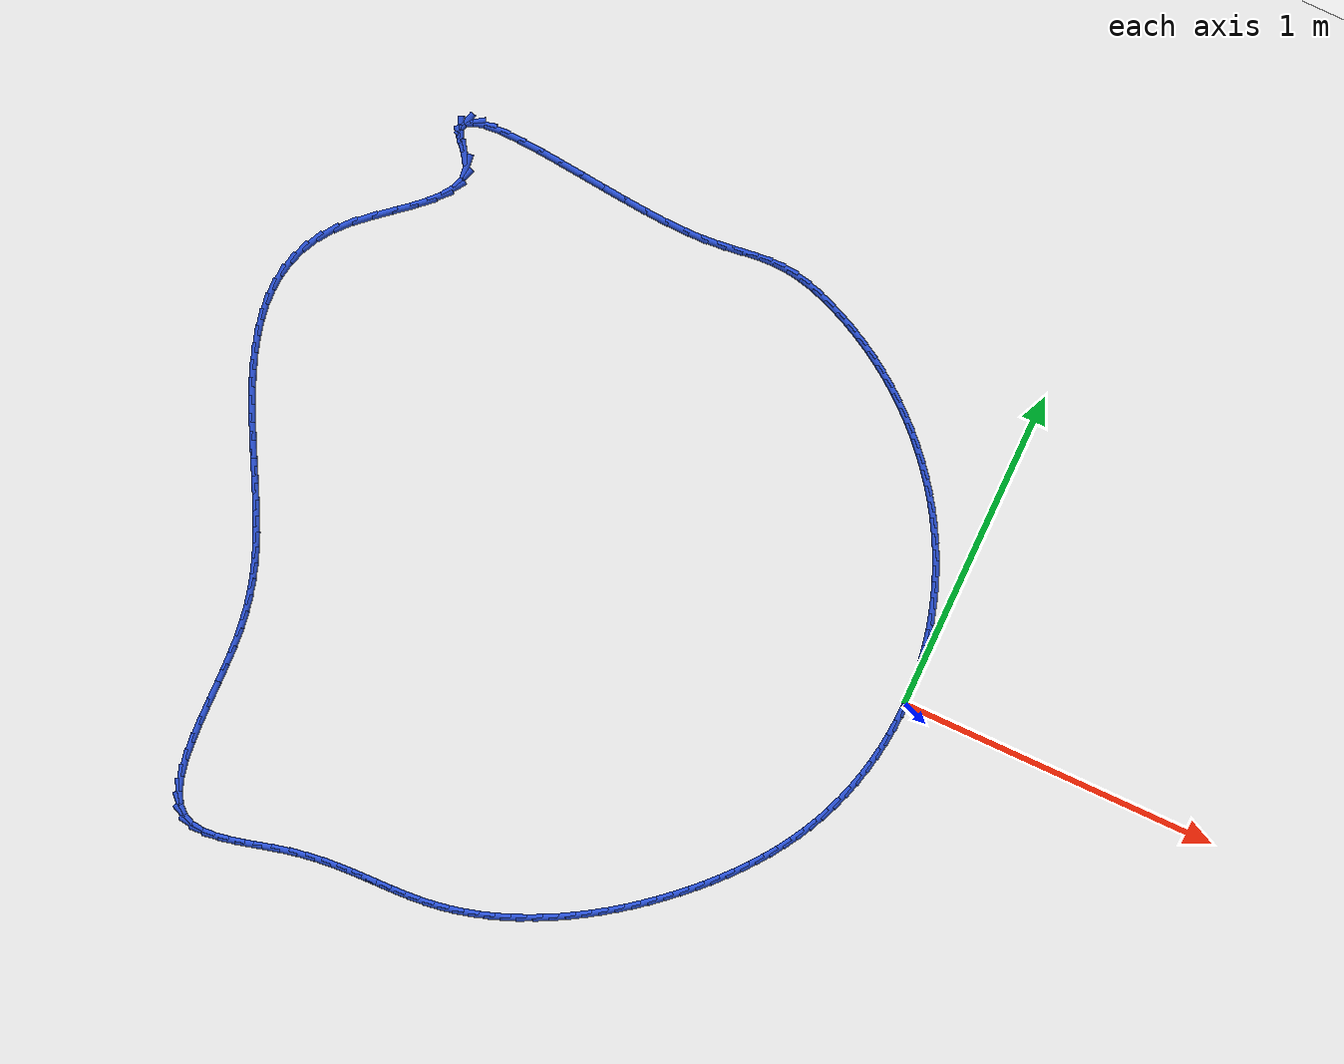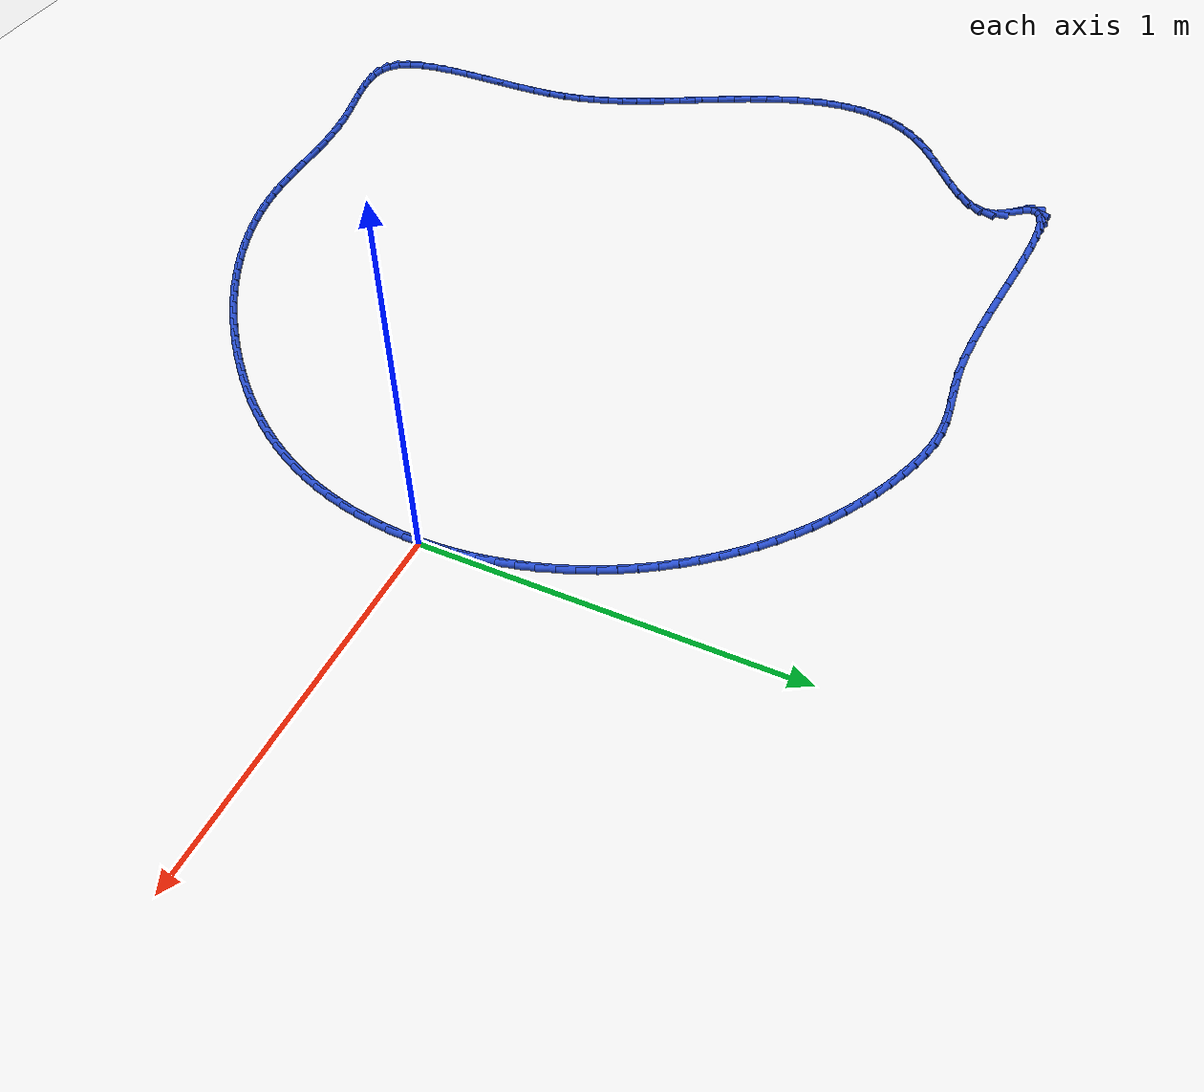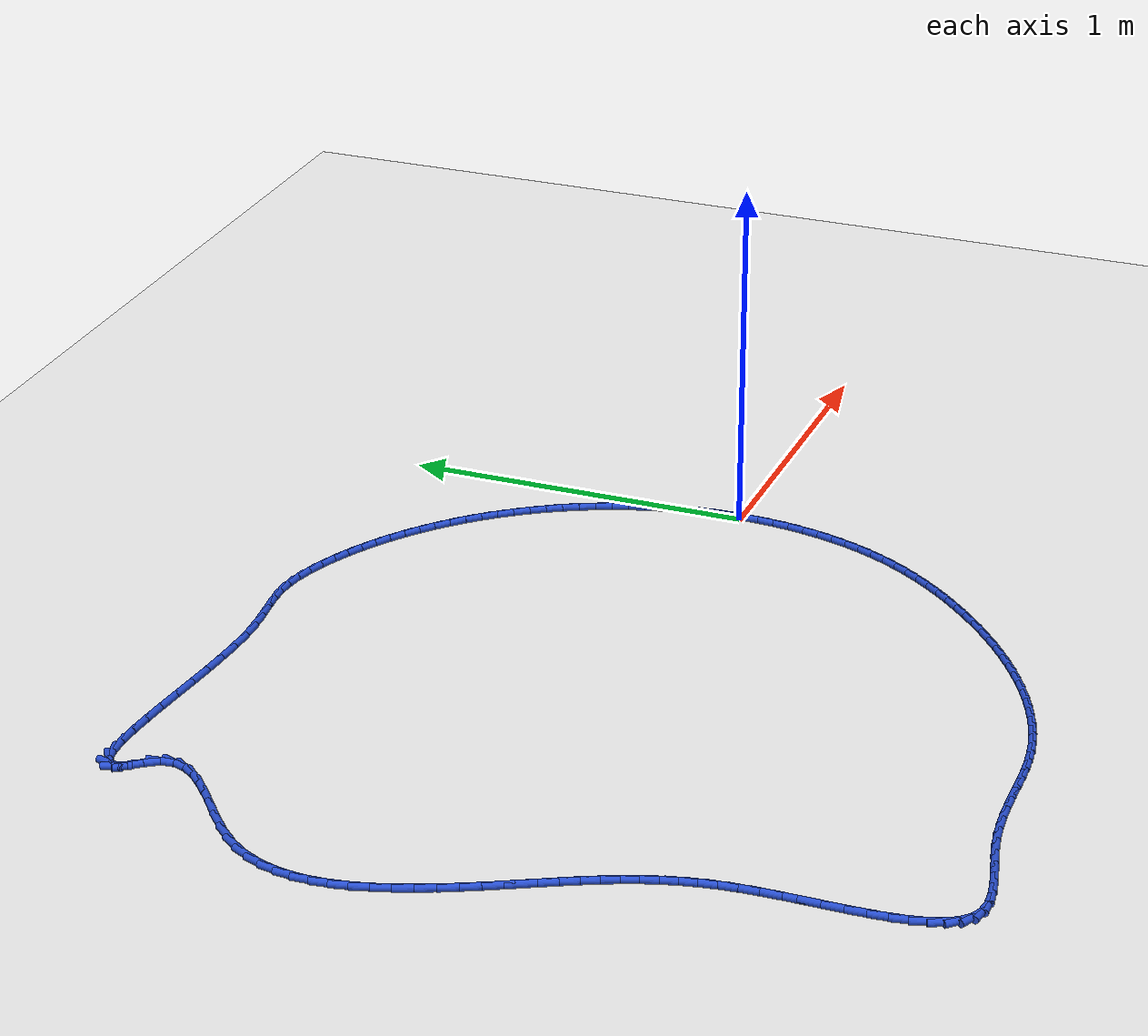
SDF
<sdf version="1.6">
 <world name="default">
  <light name="sun" type="directional">
   <pose>0 0 10 0 -0 0</pose>
   <diffuse>0.8 0.8 0.8 1</diffuse>
   <specular>0.2 0.2 0.2 1</specular>
   <attenuation>
    <range>1000</range>
    <constant>0.9</constant>
    <linear>0.01</linear>
    <quadratic>0.001</quadratic>
   </attenuation>
   <direction>-0.5 0.1 -0.9</direction>
  </light>
  <model name="ground_plane">
   <static>1</static>
   <link name="link">
    <collision name="collision">
     <geometry><plane><normal>0 0 1</normal><size>100 100</size></plane></geometry>
     <surface><friction><ode><mu>100</mu><mu2>50</mu2></ode></friction></surface>
    </collision>
    <visual name="visual">
     <cast_shadows>0</cast_shadows>
     <geometry><plane><normal>0 0 1</normal><size>100 100</size></plane></geometry>
     <material>
      <script><uri>file://media/materials/scripts/gazebo.material</uri><name>Gazebo/WhiteGlow</name></script>
     </material>
    </visual>
   </link>
  </model>
  <gravity>0 0 -9.8</gravity>
  <magnetic_field>6e-06 2.3e-05 -4.2e-05</magnetic_field>
  <atmosphere type="adiabatic"/>
  <physics name="default_physics" default="0" type="ode">
   <max_step_size>0.001</max_step_size>
   <real_time_factor>1</real_time_factor>
   <real_time_update_rate>1000</real_time_update_rate>
  </physics>
  <scene><ambient>0.4 0.4 0.4 1</ambient><background>0.7 0.7 0.7 1</background><shadows>1</shadows></scene>
  <spherical_coordinates>
   <surface_model>EARTH_WGS84</surface_model>
   <latitude_deg>0</latitude_deg>
   <longitude_deg>0</longitude_deg>
   <elevation>0</elevation>
   <heading_deg>0</heading_deg>
  </spherical_coordinates>
  <model name="line">
   <link name="link_0">
    <pose>1.3877787807814457e-17 2.7755575615628914e-17 0.01 0 1.57 -1.544613781703044</pose>
    <collision name="collision">
     <geometry><cylinder><radius>0.01</radius><length>0.08</length></cylinder></geometry>
    </collision>
    <visual name="visual">
     <material>
      <script><name>Gazebo/Blue</name><uri>file://media/materials/scripts/gazebo.material</uri></script>
     </material>
     <geometry><cylinder><radius>0.01</radius><length>0.08</length></cylinder></geometry>
    </visual>
   </link>
   <link name="link_1">
    <pose>-0.0012545301461055526 0.04790380223661767 0.01 0 1.57 -1.4966450307925274</pose>
    <collision name="collision">
     <geometry><cylinder><radius>0.01</radius><length>0.08</length></cylinder></geometry>
    </collision>
    <visual name="visual">
     <material>
      <script><name>Gazebo/Blue</name><uri>file://media/materials/scripts/gazebo.material</uri></script>
     </material>
     <geometry><cylinder><radius>0.01</radius><length>0.08</length></cylinder></geometry>
    </visual>
   </link>
   <link name="link_2">
    <pose>-0.004800251176936376 0.09563351464047144 0.01 0 1.57 -1.449062128812275</pose>
    <collision name="collision">
     <geometry><cylinder><radius>0.01</radius><length>0.08</length></cylinder></geometry>
    </collision>
    <visual name="visual">
     <material>
      <script><name>Gazebo/Blue</name><uri>file://media/materials/scripts/gazebo.material</uri></script>
     </material>
     <geometry><cylinder><radius>0.01</radius><length>0.08</length></cylinder></geometry>
    </visual>
   </link>
   <link name="link_3">
    <pose>-0.010607514842249923 0.14310208976178904 0.01 0 1.57 -1.401814430581034</pose>
    <collision name="collision">
     <geometry><cylinder><radius>0.01</radius><length>0.08</length></cylinder></geometry>
    </collision>
    <visual name="visual">
     <material>
      <script><name>Gazebo/Blue</name><uri>file://media/materials/scripts/gazebo.material</uri></script>
     </material>
     <geometry><cylinder><radius>0.01</radius><length>0.08</length></cylinder></geometry>
    </visual>
   </link>
   <link name="link_4">
    <pose>-0.018646672891803686 0.1902224801507983 0.01 0 1.57 -1.354845360949157</pose>
    <collision name="collision">
     <geometry><cylinder><radius>0.01</radius><length>0.08</length></cylinder></geometry>
    </collision>
    <visual name="visual">
     <material>
      <script><name>Gazebo/Blue</name><uri>file://media/materials/scripts/gazebo.material</uri></script>
     </material>
     <geometry><cylinder><radius>0.01</radius><length>0.08</length></cylinder></geometry>
    </visual>
   </link>
   <link name="link_5">
    <pose>-0.02888807707535513 0.23690763835772682 0.01 0 1.57 -1.308093792040413</pose>
    <collision name="collision">
     <geometry><cylinder><radius>0.01</radius><length>0.08</length></cylinder></geometry>
    </collision>
    <visual name="visual">
     <material>
      <script><name>Gazebo/Blue</name><uri>file://media/materials/scripts/gazebo.material</uri></script>
     </material>
     <geometry><cylinder><radius>0.01</radius><length>0.08</length></cylinder></geometry>
    </visual>
   </link>
   <link name="link_6">
    <pose>-0.041302079142661735 0.2830705169328024 0.01 0 1.57 -1.2614953751232447</pose>
    <collision name="collision">
     <geometry><cylinder><radius>0.01</radius><length>0.08</length></cylinder></geometry>
    </collision>
    <visual name="visual">
     <material>
      <script><name>Gazebo/Blue</name><uri>file://media/materials/scripts/gazebo.material</uri></script>
     </material>
     <geometry><cylinder><radius>0.01</radius><length>0.08</length></cylinder></geometry>
    </visual>
   </link>
   <link name="link_7">
    <pose>-0.055859030843481 0.32862406842625275 0.01 0 1.57 -1.2149838292545687</pose>
    <collision name="collision">
     <geometry><cylinder><radius>0.01</radius><length>0.08</length></cylinder></geometry>
    </collision>
    <visual name="visual">
     <material>
      <script><name>Gazebo/Blue</name><uri>file://media/materials/scripts/gazebo.material</uri></script>
     </material>
     <geometry><cylinder><radius>0.01</radius><length>0.08</length></cylinder></geometry>
    </visual>
   </link>
   <link name="link_8">
    <pose>-0.07252928392757041 0.3734812453883056 0.01 0 1.57 -1.1684940254506615</pose>
    <collision name="collision">
     <geometry><cylinder><radius>0.01</radius><length>0.08</length></cylinder></geometry>
    </collision>
    <visual name="visual">
     <material>
      <script><name>Gazebo/Blue</name><uri>file://media/materials/scripts/gazebo.material</uri></script>
     </material>
     <geometry><cylinder><radius>0.01</radius><length>0.08</length></cylinder></geometry>
    </visual>
   </link>
   <link name="link_9">
    <pose>-0.09128311318735405 0.417555043475024 0.01 0 1.57 -1.1221879623194562</pose>
    <collision name="collision">
     <geometry><cylinder><radius>0.01</radius><length>0.08</length></cylinder></geometry>
    </collision>
    <visual name="visual">
     <material>
      <script><name>Gazebo/Blue</name><uri>file://media/materials/scripts/gazebo.material</uri></script>
     </material>
     <geometry><cylinder><radius>0.01</radius><length>0.08</length></cylinder></geometry>
    </visual>
   </link>
   <link name="link_10">
    <pose>-0.1120812197816867 0.46076382078752925 0.01 0 1.57 -1.0764483833147556</pose>
    <collision name="collision">
     <geometry><cylinder><radius>0.01</radius><length>0.08</length></cylinder></geometry>
    </collision>
    <visual name="visual">
     <material>
      <script><name>Gazebo/Blue</name><uri>file://media/materials/scripts/gazebo.material</uri></script>
     </material>
     <geometry><cylinder><radius>0.01</radius><length>0.08</length></cylinder></geometry>
    </visual>
   </link>
   <link name="link_11">
    <pose>-0.13486556895129687 0.5030364299096123 0.01 0 1.57 -1.0312596849297924</pose>
    <collision name="collision">
     <geometry><cylinder><radius>0.01</radius><length>0.08</length></cylinder></geometry>
    </collision>
    <visual name="visual">
     <material>
      <script><name>Gazebo/Blue</name><uri>file://media/materials/scripts/gazebo.material</uri></script>
     </material>
     <geometry><cylinder><radius>0.01</radius><length>0.08</length></cylinder></geometry>
    </visual>
   </link>
   <link name="link_12">
    <pose>-0.15957595327795984 0.5443029403887356 0.01 0 1.57 -0.9865486678693791</pose>
    <collision name="collision">
     <geometry><cylinder><radius>0.01</radius><length>0.08</length></cylinder></geometry>
    </collision>
    <visual name="visual">
     <material>
      <script><name>Gazebo/Blue</name><uri>file://media/materials/scripts/gazebo.material</uri></script>
     </material>
     <geometry><cylinder><radius>0.01</radius><length>0.08</length></cylinder></geometry>
    </visual>
   </link>
   <link name="link_13">
    <pose>-0.18615216534345114 0.5844934217723623 0.01 0 1.57 -0.9422376761508325</pose>
    <collision name="collision">
     <geometry><cylinder><radius>0.01</radius><length>0.08</length></cylinder></geometry>
    </collision>
    <visual name="visual">
     <material>
      <script><name>Gazebo/Blue</name><uri>file://media/materials/scripts/gazebo.material</uri></script>
     </material>
     <geometry><cylinder><radius>0.01</radius><length>0.08</length></cylinder></geometry>
    </visual>
   </link>
   <link name="link_14">
    <pose>-0.21453399772954612 0.6235379436079551 0.01 0 1.57 -0.8982459065295604</pose>
    <collision name="collision">
     <geometry><cylinder><radius>0.01</radius><length>0.08</length></cylinder></geometry>
    </collision>
    <visual name="visual">
     <material>
      <script><name>Gazebo/Blue</name><uri>file://media/materials/scripts/gazebo.material</uri></script>
     </material>
     <geometry><cylinder><radius>0.01</radius><length>0.08</length></cylinder></geometry>
    </visual>
   </link>
   <link name="link_15">
    <pose>-0.24466124301802022 0.6613665754429768 0.01 0 1.57 -0.8544905910481302</pose>
    <collision name="collision">
     <geometry><cylinder><radius>0.01</radius><length>0.08</length></cylinder></geometry>
    </collision>
    <visual name="visual">
     <material>
      <script><name>Gazebo/Blue</name><uri>file://media/materials/scripts/gazebo.material</uri></script>
     </material>
     <geometry><cylinder><radius>0.01</radius><length>0.08</length></cylinder></geometry>
    </visual>
   </link>
   <link name="link_16">
    <pose>-0.2764736937906489 0.6979093868248906 0.01 0 1.57 -0.8108880752443167</pose>
    <collision name="collision">
     <geometry><cylinder><radius>0.01</radius><length>0.08</length></cylinder></geometry>
    </collision>
    <visual name="visual">
     <material>
      <script><name>Gazebo/Blue</name><uri>file://media/materials/scripts/gazebo.material</uri></script>
     </material>
     <geometry><cylinder><radius>0.01</radius><length>0.08</length></cylinder></geometry>
    </visual>
   </link>
   <link name="link_17">
    <pose>-0.30991114262920744 0.7330964473011591 0.01 0 1.57 -0.7673548182199115</pose>
    <collision name="collision">
     <geometry><cylinder><radius>0.01</radius><length>0.08</length></cylinder></geometry>
    </collision>
    <visual name="visual">
     <material>
      <script><name>Gazebo/Blue</name><uri>file://media/materials/scripts/gazebo.material</uri></script>
     </material>
     <geometry><cylinder><radius>0.01</radius><length>0.08</length></cylinder></geometry>
    </visual>
   </link>
   <link name="link_18">
    <pose>-0.34491338211547146 0.7668578264192449 0.01 0 1.57 -0.7238083423661128</pose>
    <collision name="collision">
     <geometry><cylinder><radius>0.01</radius><length>0.08</length></cylinder></geometry>
    </collision>
    <visual name="visual">
     <material>
      <script><name>Gazebo/Blue</name><uri>file://media/materials/scripts/gazebo.material</uri></script>
     </material>
     <geometry><cylinder><radius>0.01</radius><length>0.08</length></cylinder></geometry>
    </visual>
   </link>
   <link name="link_19">
    <pose>-0.3814202048312162 0.7991235937266113 0.01 0 1.57 -0.6801681604246306</pose>
    <collision name="collision">
     <geometry><cylinder><radius>0.01</radius><length>0.08</length></cylinder></geometry>
    </collision>
    <visual name="visual">
     <material>
      <script><name>Gazebo/Blue</name><uri>file://media/materials/scripts/gazebo.material</uri></script>
     </material>
     <geometry><cylinder><radius>0.01</radius><length>0.08</length></cylinder></geometry>
    </visual>
   </link>
   <link name="link_20">
    <pose>-0.4193714033582171 0.829823818770721 0.01 0 1.57 -0.6363567059710581</pose>
    <collision name="collision">
     <geometry><cylinder><radius>0.01</radius><length>0.08</length></cylinder></geometry>
    </collision>
    <visual name="visual">
     <material>
      <script><name>Gazebo/Blue</name><uri>file://media/materials/scripts/gazebo.material</uri></script>
     </material>
     <geometry><cylinder><radius>0.01</radius><length>0.08</length></cylinder></geometry>
    </visual>
   </link>
   <link name="link_21">
    <pose>-0.4587067702782499 0.8588885710990372 0.01 0 1.57 -0.5923002904441449</pose>
    <collision name="collision">
     <geometry><cylinder><radius>0.01</radius><length>0.08</length></cylinder></geometry>
    </collision>
    <visual name="visual">
     <material>
      <script><name>Gazebo/Blue</name><uri>file://media/materials/scripts/gazebo.material</uri></script>
     </material>
     <geometry><cylinder><radius>0.01</radius><length>0.08</length></cylinder></geometry>
    </visual>
   </link>
   <link name="link_22">
    <pose>-0.4993660981730894 0.8862479202590219 0.01 0 1.57 -0.5479301055080513</pose>
    <collision name="collision">
     <geometry><cylinder><radius>0.01</radius><length>0.08</length></cylinder></geometry>
    </collision>
    <visual name="visual">
     <material>
      <script><name>Gazebo/Blue</name><uri>file://media/materials/scripts/gazebo.material</uri></script>
     </material>
     <geometry><cylinder><radius>0.01</radius><length>0.08</length></cylinder></geometry>
    </visual>
   </link>
   <link name="link_23">
    <pose>-0.5412891796245116 0.9118319357981388 0.01 0 1.57 -0.5031832837380661</pose>
    <collision name="collision">
     <geometry><cylinder><radius>0.01</radius><length>0.08</length></cylinder></geometry>
    </collision>
    <visual name="visual">
     <material>
      <script><name>Gazebo/Blue</name><uri>file://media/materials/scripts/gazebo.material</uri></script>
     </material>
     <geometry><cylinder><radius>0.01</radius><length>0.08</length></cylinder></geometry>
    </visual>
   </link>
   <link name="link_24">
    <pose>-0.5844158072142918 0.9355706872638505 0.01 0 1.57 -0.4580040232441666</pose>
    <collision name="collision">
     <geometry><cylinder><radius>0.01</radius><length>0.08</length></cylinder></geometry>
    </collision>
    <visual name="visual">
     <material>
      <script><name>Gazebo/Blue</name><uri>file://media/materials/scripts/gazebo.material</uri></script>
     </material>
     <geometry><cylinder><radius>0.01</radius><length>0.08</length></cylinder></geometry>
    </visual>
   </link>
   <link name="link_25">
    <pose>-0.6286857735242052 0.9573942442036198 0.01 0 1.57 -0.4123173153655327</pose>
    <collision name="collision">
     <geometry><cylinder><radius>0.01</radius><length>0.08</length></cylinder></geometry>
    </collision>
    <visual name="visual">
     <material>
      <script><name>Gazebo/Blue</name><uri>file://media/materials/scripts/gazebo.material</uri></script>
     </material>
     <geometry><cylinder><radius>0.01</radius><length>0.08</length></cylinder></geometry>
    </visual>
   </link>
   <link name="link_26">
    <pose>-0.6740368422993958 0.977230305243397 0.01 0 1.57 -0.363218448490127</pose>
    <collision name="collision">
     <geometry><cylinder><radius>0.01</radius><length>0.08</length></cylinder></geometry>
    </collision>
    <visual name="visual">
     <material>
      <script><name>Gazebo/Blue</name><uri>file://media/materials/scripts/gazebo.material</uri></script>
     </material>
     <geometry><cylinder><radius>0.01</radius><length>0.08</length></cylinder></geometry>
    </visual>
   </link>
   <link name="link_27">
    <pose>-0.7202141435150312 0.994781454999369 0.01 0 1.57 -0.30409028890825146</pose>
    <collision name="collision">
     <geometry><cylinder><radius>0.01</radius><length>0.08</length></cylinder></geometry>
    </collision>
    <visual name="visual">
     <material>
      <script><name>Gazebo/Blue</name><uri>file://media/materials/scripts/gazebo.material</uri></script>
     </material>
     <geometry><cylinder><radius>0.01</radius><length>0.08</length></cylinder></geometry>
    </visual>
   </link>
   <link name="link_28">
    <pose>-0.7666141972449155 1.0093428886006715 0.01 0 1.57 -0.2311849519460141</pose>
    <collision name="collision">
     <geometry><cylinder><radius>0.01</radius><length>0.08</length></cylinder></geometry>
    </collision>
    <visual name="visual">
     <material>
      <script><name>Gazebo/Blue</name><uri>file://media/materials/scripts/gazebo.material</uri></script>
     </material>
     <geometry><cylinder><radius>0.01</radius><length>0.08</length></cylinder></geometry>
    </visual>
   </link>
   <link name="link_29">
    <pose>-0.8125968155633818 1.020166903791665 0.01 0 1.57 -0.1401741466219949</pose>
    <collision name="collision">
     <geometry><cylinder><radius>0.01</radius><length>0.08</length></cylinder></geometry>
    </collision>
    <visual name="visual">
     <material>
      <script><name>Gazebo/Blue</name><uri>file://media/materials/scripts/gazebo.material</uri></script>
     </material>
     <geometry><cylinder><radius>0.01</radius><length>0.08</length></cylinder></geometry>
    </visual>
   </link>
   <link name="link_30">
    <pose>-0.8575218105447635 1.0265057983167116 0.01 0 1.57 -0.03166653991331851</pose>
    <collision name="collision">
     <geometry><cylinder><radius>0.01</radius><length>0.08</length></cylinder></geometry>
    </collision>
    <visual name="visual">
     <material>
      <script><name>Gazebo/Blue</name><uri>file://media/materials/scripts/gazebo.material</uri></script>
     </material>
     <geometry><cylinder><radius>0.01</radius><length>0.08</length></cylinder></geometry>
    </visual>
   </link>
   <link name="link_31">
    <pose>-0.9010011932040216 1.0278831003261408 0.01 0 1.57 0.06016790640704173</pose>
    <collision name="collision">
     <geometry><cylinder><radius>0.01</radius><length>0.08</length></cylinder></geometry>
    </collision>
    <visual name="visual">
     <material>
      <script><name>Gazebo/Blue</name><uri>file://media/materials/scripts/gazebo.material</uri></script>
     </material>
     <geometry><cylinder><radius>0.01</radius><length>0.08</length></cylinder></geometry>
    </visual>
   </link>
   <link name="link_32">
    <pose>-0.9440135247209106 1.02529201090012 0.01 0 1.57 0.11477950097939665</pose>
    <collision name="collision">
     <geometry><cylinder><radius>0.01</radius><length>0.08</length></cylinder></geometry>
    </collision>
    <visual name="visual">
     <material>
      <script><name>Gazebo/Blue</name><uri>file://media/materials/scripts/gazebo.material</uri></script>
     </material>
     <geometry><cylinder><radius>0.01</radius><length>0.08</length></cylinder></geometry>
    </visual>
   </link>
   <link name="link_33">
    <pose>-0.9879980686975288 1.0202211991201169 0.01 0 1.57 0.12990989950993476</pose>
    <collision name="collision">
     <geometry><cylinder><radius>0.01</radius><length>0.08</length></cylinder></geometry>
    </collision>
    <visual name="visual">
     <material>
      <script><name>Gazebo/Blue</name><uri>file://media/materials/scripts/gazebo.material</uri></script>
     </material>
     <geometry><cylinder><radius>0.01</radius><length>0.08</length></cylinder></geometry>
    </visual>
   </link>
   <link name="link_34">
    <pose>-1.0343944415497703 1.0141597135054707 0.01 0 1.57 0.11026442447605785</pose>
    <collision name="collision">
     <geometry><cylinder><radius>0.01</radius><length>0.08</length></cylinder></geometry>
    </collision>
    <visual name="visual">
     <material>
      <script><name>Gazebo/Blue</name><uri>file://media/materials/scripts/gazebo.material</uri></script>
     </material>
     <geometry><cylinder><radius>0.01</radius><length>0.08</length></cylinder></geometry>
    </visual>
   </link>
   <link name="link_35">
    <pose>-1.0846422596935301 1.0085966025755213 0.01 0 1.57 0.0642929704911061</pose>
    <collision name="collision">
     <geometry><cylinder><radius>0.01</radius><length>0.08</length></cylinder></geometry>
    </collision>
    <visual name="visual">
     <material>
      <script><name>Gazebo/Blue</name><uri>file://media/materials/scripts/gazebo.material</uri></script>
     </material>
     <geometry><cylinder><radius>0.01</radius><length>0.08</length></cylinder></geometry>
    </visual>
   </link>
   <link name="link_36">
    <pose>-1.1401811395447028 1.0050209148496083 0.01 0 1.57 0.005919473220937264</pose>
    <collision name="collision">
     <geometry><cylinder><radius>0.01</radius><length>0.08</length></cylinder></geometry>
    </collision>
    <visual name="visual">
     <material>
      <script><name>Gazebo/Blue</name><uri>file://media/materials/scripts/gazebo.material</uri></script>
     </material>
     <geometry><cylinder><radius>0.01</radius><length>0.08</length></cylinder></geometry>
    </visual>
   </link>
   <link name="link_37">
    <pose>-1.2020818807285722 1.0046544907899513 0.01 0 1.57 -0.038667322725978615</pose>
    <collision name="collision">
     <geometry><cylinder><radius>0.01</radius><length>0.08</length></cylinder></geometry>
    </collision>
    <visual name="visual">
     <material>
      <script><name>Gazebo/Blue</name><uri>file://media/materials/scripts/gazebo.material</uri></script>
     </material>
     <geometry><cylinder><radius>0.01</radius><length>0.08</length></cylinder></geometry>
    </visual>
   </link>
   <link name="link_38">
    <pose>-1.2693995676604886 1.00725878359152 0.01 0 1.57 -0.06796469117677396</pose>
    <collision name="collision">
     <geometry><cylinder><radius>0.01</radius><length>0.08</length></cylinder></geometry>
    </collision>
    <visual name="visual">
     <material>
      <script><name>Gazebo/Blue</name><uri>file://media/materials/scripts/gazebo.material</uri></script>
     </material>
     <geometry><cylinder><radius>0.01</radius><length>0.08</length></cylinder></geometry>
    </visual>
   </link>
   <link name="link_39">
    <pose>-1.3405041096082462 1.0120988365118149 0.01 0 1.57 -0.08633118568464455</pose>
    <collision name="collision">
     <geometry><cylinder><radius>0.01</radius><length>0.08</length></cylinder></geometry>
    </collision>
    <visual name="visual">
     <material>
      <script><name>Gazebo/Blue</name><uri>file://media/materials/scripts/gazebo.material</uri></script>
     </material>
     <geometry><cylinder><radius>0.01</radius><length>0.08</length></cylinder></geometry>
    </visual>
   </link>
   <link name="link_40">
    <pose>-1.4137648500109297 1.0184392828649849 0.01 0 1.57 -0.09600200108081187</pose>
    <collision name="collision">
     <geometry><cylinder><radius>0.01</radius><length>0.08</length></cylinder></geometry>
    </collision>
    <visual name="visual">
     <material>
      <script><name>Gazebo/Blue</name><uri>file://media/materials/scripts/gazebo.material</uri></script>
     </material>
     <geometry><cylinder><radius>0.01</radius><length>0.08</length></cylinder></geometry>
    </visual>
   </link>
   <link name="link_41">
    <pose>-1.4875511323076231 1.0255447559651796 0.01 0 1.57 -0.09785675748230672</pose>
    <collision name="collision">
     <geometry><cylinder><radius>0.01</radius><length>0.08</length></cylinder></geometry>
    </collision>
    <visual name="visual">
     <material>
      <script><name>Gazebo/Blue</name><uri>file://media/materials/scripts/gazebo.material</uri></script>
     </material>
     <geometry><cylinder><radius>0.01</radius><length>0.08</length></cylinder></geometry>
    </visual>
   </link>
   <link name="link_42">
    <pose>-1.5602322999374094 1.032679889126549 0.01 0 1.57 -0.09166306632178006</pose>
    <collision name="collision">
     <geometry><cylinder><radius>0.01</radius><length>0.08</length></cylinder></geometry>
    </collision>
    <visual name="visual">
     <material>
      <script><name>Gazebo/Blue</name><uri>file://media/materials/scripts/gazebo.material</uri></script>
     </material>
     <geometry><cylinder><radius>0.01</radius><length>0.08</length></cylinder></geometry>
    </visual>
   </link>
   <link name="link_43">
    <pose>-1.6301776963393726 1.0391093156632418 0.01 0 1.57 -0.07592015509825249</pose>
    <collision name="collision">
     <geometry><cylinder><radius>0.01</radius><length>0.08</length></cylinder></geometry>
    </collision>
    <visual name="visual">
     <material>
      <script><name>Gazebo/Blue</name><uri>file://media/materials/scripts/gazebo.material</uri></script>
     </material>
     <geometry><cylinder><radius>0.01</radius><length>0.08</length></cylinder></geometry>
    </visual>
   </link>
   <link name="link_44">
    <pose>-1.6957566649525961 1.0440976688894077 0.01 0 1.57 -0.04715910562345982</pose>
    <collision name="collision">
     <geometry><cylinder><radius>0.01</radius><length>0.08</length></cylinder></geometry>
    </collision>
    <visual name="visual">
     <material>
      <script><name>Gazebo/Blue</name><uri>file://media/materials/scripts/gazebo.material</uri></script>
     </material>
     <geometry><cylinder><radius>0.01</radius><length>0.08</length></cylinder></geometry>
    </visual>
   </link>
   <link name="link_45">
    <pose>-1.7553385492161648 1.0469095821191967 0.01 0 1.57 0.0019227211324223659</pose>
    <collision name="collision">
     <geometry><cylinder><radius>0.01</radius><length>0.08</length></cylinder></geometry>
    </collision>
    <visual name="visual">
     <material>
      <script><name>Gazebo/Blue</name><uri>file://media/materials/scripts/gazebo.material</uri></script>
     </material>
     <geometry><cylinder><radius>0.01</radius><length>0.08</length></cylinder></geometry>
    </visual>
   </link>
   <link name="link_46">
    <pose>-1.8072926925691615 1.0468096886667577 0.01 0 1.57 0.08753778072464134</pose>
    <collision name="collision">
     <geometry><cylinder><radius>0.01</radius><length>0.08</length></cylinder></geometry>
    </collision>
    <visual name="visual">
     <material>
      <script><name>Gazebo/Blue</name><uri>file://media/materials/scripts/gazebo.material</uri></script>
     </material>
     <geometry><cylinder><radius>0.01</radius><length>0.08</length></cylinder></geometry>
    </visual>
   </link>
   <link name="link_47">
    <pose>-1.8499884384506704 1.0430626218462409 0.01 0 1.57 0.25023684984336253</pose>
    <collision name="collision">
     <geometry><cylinder><radius>0.01</radius><length>0.08</length></cylinder></geometry>
    </collision>
    <visual name="visual">
     <material>
      <script><name>Gazebo/Blue</name><uri>file://media/materials/scripts/gazebo.material</uri></script>
     </material>
     <geometry><cylinder><radius>0.01</radius><length>0.08</length></cylinder></geometry>
    </visual>
   </link>
   <link name="link_48">
    <pose>-1.8817951302997755 1.0349330149717952 0.01 0 1.57 0.6018546590014139</pose>
    <collision name="collision">
     <geometry><cylinder><radius>0.01</radius><length>0.08</length></cylinder></geometry>
    </collision>
    <visual name="visual">
     <material>
      <script><name>Gazebo/Blue</name><uri>file://media/materials/scripts/gazebo.material</uri></script>
     </material>
     <geometry><cylinder><radius>0.01</radius><length>0.08</length></cylinder></geometry>
    </visual>
   </link>
   <link name="link_49">
    <pose>-1.90108211155556 1.0216855013575705 0.01 0 1.57 1.3080898965298342</pose>
    <collision name="collision">
     <geometry><cylinder><radius>0.01</radius><length>0.08</length></cylinder></geometry>
    </collision>
    <visual name="visual">
     <material>
      <script><name>Gazebo/Blue</name><uri>file://media/materials/scripts/gazebo.material</uri></script>
     </material>
     <geometry><cylinder><radius>0.01</radius><length>0.08</length></cylinder></geometry>
    </visual>
   </link>
   <link name="link_50">
    <pose>-1.9062187256571086 1.0025847143177162 0.01 0 1.57 -1.1779809442990818</pose>
    <collision name="collision">
     <geometry><cylinder><radius>0.01</radius><length>0.08</length></cylinder></geometry>
    </collision>
    <visual name="visual">
     <material>
      <script><name>Gazebo/Blue</name><uri>file://media/materials/scripts/gazebo.material</uri></script>
     </material>
     <geometry><cylinder><radius>0.01</radius><length>0.08</length></cylinder></geometry>
    </visual>
   </link>
   <link name="link_51">
    <pose>-1.8955743160435041 0.9768952871663817 0.01 0 1.57 -0.8757549765913629</pose>
    <collision name="collision">
     <geometry><cylinder><radius>0.01</radius><length>0.08</length></cylinder></geometry>
    </collision>
    <visual name="visual">
     <material>
      <script><name>Gazebo/Blue</name><uri>file://media/materials/scripts/gazebo.material</uri></script>
     </material>
     <geometry><cylinder><radius>0.01</radius><length>0.08</length></cylinder></geometry>
    </visual>
   </link>
   <link name="link_52">
    <pose>-1.8681526677762452 0.9440095801986798 0.01 0 1.57 -0.9882359674177307</pose>
    <collision name="collision">
     <geometry><cylinder><radius>0.01</radius><length>0.08</length></cylinder></geometry>
    </collision>
    <visual name="visual">
     <material>
      <script><name>Gazebo/Blue</name><uri>file://media/materials/scripts/gazebo.material</uri></script>
     </material>
     <geometry><cylinder><radius>0.01</radius><length>0.08</length></cylinder></geometry>
    </visual>
   </link>
   <link name="link_53">
    <pose>-1.8441940039656126 0.9076443284974955 0.01 0 1.57 -1.461314443597476</pose>
    <collision name="collision">
     <geometry><cylinder><radius>0.01</radius><length>0.08</length></cylinder></geometry>
    </collision>
    <visual name="visual">
     <material>
      <script><name>Gazebo/Blue</name><uri>file://media/materials/scripts/gazebo.material</uri></script>
     </material>
     <geometry><cylinder><radius>0.01</radius><length>0.08</length></cylinder></geometry>
    </visual>
   </link>
   <link name="link_54">
    <pose>-1.8401979832700692 0.8712908972688056 0.01 0 1.57 1.2299641560198242</pose>
    <collision name="collision">
     <geometry><cylinder><radius>0.01</radius><length>0.08</length></cylinder></geometry>
    </collision>
    <visual name="visual">
     <material>
      <script><name>Gazebo/Blue</name><uri>file://media/materials/scripts/gazebo.material</uri></script>
     </material>
     <geometry><cylinder><radius>0.01</radius><length>0.08</length></cylinder></geometry>
    </visual>
   </link>
   <link name="link_55">
    <pose>-1.8531299030066841 0.8348294153393331 0.01 0 1.57 0.9456995383966647</pose>
    <collision name="collision">
     <geometry><cylinder><radius>0.01</radius><length>0.08</length></cylinder></geometry>
    </collision>
    <visual name="visual">
     <material>
      <script><name>Gazebo/Blue</name><uri>file://media/materials/scripts/gazebo.material</uri></script>
     </material>
     <geometry><cylinder><radius>0.01</radius><length>0.08</length></cylinder></geometry>
    </visual>
   </link>
   <link name="link_56">
    <pose>-1.8796475214973603 0.7980826629983471 0.01 0 1.57 0.7914568288842002</pose>
    <collision name="collision">
     <geometry><cylinder><radius>0.01</radius><length>0.08</length></cylinder></geometry>
    </collision>
    <visual name="visual">
     <material>
      <script><name>Gazebo/Blue</name><uri>file://media/materials/scripts/gazebo.material</uri></script>
     </material>
     <geometry><cylinder><radius>0.01</radius><length>0.08</length></cylinder></geometry>
    </visual>
   </link>
   <link name="link_57">
    <pose>-1.9164085970639995 0.7608734205351182 0.01 0 1.57 0.7141992470686699</pose>
    <collision name="collision">
     <geometry><cylinder><radius>0.01</radius><length>0.08</length></cylinder></geometry>
    </collision>
    <visual name="visual">
     <material>
      <script><name>Gazebo/Blue</name><uri>file://media/materials/scripts/gazebo.material</uri></script>
     </material>
     <geometry><cylinder><radius>0.01</radius><length>0.08</length></cylinder></geometry>
    </visual>
   </link>
   <link name="link_58">
    <pose>-1.9600708880285058 0.7230244682389161 0.01 0 1.57 0.6861137716250008</pose>
    <collision name="collision">
     <geometry><cylinder><radius>0.01</radius><length>0.08</length></cylinder></geometry>
    </collision>
    <visual name="visual">
     <material>
      <script><name>Gazebo/Blue</name><uri>file://media/materials/scripts/gazebo.material</uri></script>
     </material>
     <geometry><cylinder><radius>0.01</radius><length>0.08</length></cylinder></geometry>
    </visual>
   </link>
   <link name="link_59">
    <pose>-2.00729215271278 0.6843585863990116 0.01 0 1.57 0.6963331351956438</pose>
    <collision name="collision">
     <geometry><cylinder><radius>0.01</radius><length>0.08</length></cylinder></geometry>
    </collision>
    <visual name="visual">
     <material>
      <script><name>Gazebo/Blue</name><uri>file://media/materials/scripts/gazebo.material</uri></script>
     </material>
     <geometry><cylinder><radius>0.01</radius><length>0.08</length></cylinder></geometry>
    </visual>
   </link>
   <link name="link_60">
    <pose>-2.0547301494387264 0.6446985553046746 0.01 0 1.57 0.7445361653085348</pose>
    <collision name="collision">
     <geometry><cylinder><radius>0.01</radius><length>0.08</length></cylinder></geometry>
    </collision>
    <visual name="visual">
     <material>
      <script><name>Gazebo/Blue</name><uri>file://media/materials/scripts/gazebo.material</uri></script>
     </material>
     <geometry><cylinder><radius>0.01</radius><length>0.08</length></cylinder></geometry>
    </visual>
   </link>
   <link name="link_61">
    <pose>-2.0990426365282473 0.6038671552451751 0.01 0 1.57 0.8386759127549288</pose>
    <collision name="collision">
     <geometry><cylinder><radius>0.01</radius><length>0.08</length></cylinder></geometry>
    </collision>
    <visual name="visual">
     <material>
      <script><name>Gazebo/Blue</name><uri>file://media/materials/scripts/gazebo.material</uri></script>
     </material>
     <geometry><cylinder><radius>0.01</radius><length>0.08</length></cylinder></geometry>
    </visual>
   </link>
   <link name="link_62">
    <pose>-2.13694707238571 0.5616922298648667 0.01 0 1.57 0.9680977700913777</pose>
    <collision name="collision">
     <geometry><cylinder><radius>0.01</radius><length>0.08</length></cylinder></geometry>
    </collision>
    <visual name="visual">
     <material>
      <script><name>Gazebo/Blue</name><uri>file://media/materials/scripts/gazebo.material</uri></script>
     </material>
     <geometry><cylinder><radius>0.01</radius><length>0.08</length></cylinder></geometry>
    </visual>
   </link>
   <link name="link_63">
    <pose>-2.1669088214377776 0.5181498683126117 0.01 0 1.57 1.105588465226603</pose>
    <collision name="collision">
     <geometry><cylinder><radius>0.01</radius><length>0.08</length></cylinder></geometry>
    </collision>
    <visual name="visual">
     <material>
      <script><name>Gazebo/Blue</name><uri>file://media/materials/scripts/gazebo.material</uri></script>
     </material>
     <geometry><cylinder><radius>0.01</radius><length>0.08</length></cylinder></geometry>
    </visual>
   </link>
   <link name="link_64">
    <pose>-2.1893788478975775 0.47338456481073626 0.01 0 1.57 1.2439777994695138</pose>
    <collision name="collision">
     <geometry><cylinder><radius>0.01</radius><length>0.08</length></cylinder></geometry>
    </collision>
    <visual name="visual">
     <material>
      <script><name>Gazebo/Blue</name><uri>file://media/materials/scripts/gazebo.material</uri></script>
     </material>
     <geometry><cylinder><radius>0.01</radius><length>0.08</length></cylinder></geometry>
    </visual>
   </link>
   <link name="link_65">
    <pose>-2.2049155972113463 0.42754992940897635 0.01 0 1.57 1.377273601056704</pose>
    <collision name="collision">
     <geometry><cylinder><radius>0.01</radius><length>0.08</length></cylinder></geometry>
    </collision>
    <visual name="visual">
     <material>
      <script><name>Gazebo/Blue</name><uri>file://media/materials/scripts/gazebo.material</uri></script>
     </material>
     <geometry><cylinder><radius>0.01</radius><length>0.08</length></cylinder></geometry>
    </visual>
   </link>
   <link name="link_66">
    <pose>-2.214077514825319 0.3807995721570676 0.01 0 1.57 1.5004985994566409</pose>
    <collision name="collision">
     <geometry><cylinder><radius>0.01</radius><length>0.08</length></cylinder></geometry>
    </collision>
    <visual name="visual">
     <material>
      <script><name>Gazebo/Blue</name><uri>file://media/materials/scripts/gazebo.material</uri></script>
     </material>
     <geometry><cylinder><radius>0.01</radius><length>0.08</length></cylinder></geometry>
    </visual>
   </link>
   <link name="link_67">
    <pose>-2.217423046185731 0.33328710310474585 0.01 0 1.57 -1.5310755242796392</pose>
    <collision name="collision">
     <geometry><cylinder><radius>0.01</radius><length>0.08</length></cylinder></geometry>
    </collision>
    <visual name="visual">
     <material>
      <script><name>Gazebo/Blue</name><uri>file://media/materials/scripts/gazebo.material</uri></script>
     </material>
     <geometry><cylinder><radius>0.01</radius><length>0.08</length></cylinder></geometry>
    </visual>
   </link>
   <link name="link_68">
    <pose>-2.2155106367388187 0.2851661323017476 0.01 0 1.57 -1.435512692355467</pose>
    <collision name="collision">
     <geometry><cylinder><radius>0.01</radius><length>0.08</length></cylinder></geometry>
    </collision>
    <visual name="visual">
     <material>
      <script><name>Gazebo/Blue</name><uri>file://media/materials/scripts/gazebo.material</uri></script>
     </material>
     <geometry><cylinder><radius>0.01</radius><length>0.08</length></cylinder></geometry>
    </visual>
   </link>
   <link name="link_69">
    <pose>-2.2088987319308173 0.23659026979780842 0.01 0 1.57 -1.3542463534025677</pose>
    <collision name="collision">
     <geometry><cylinder><radius>0.01</radius><length>0.08</length></cylinder></geometry>
    </collision>
    <visual name="visual">
     <material>
      <script><name>Gazebo/Blue</name><uri>file://media/materials/scripts/gazebo.material</uri></script>
     </material>
     <geometry><cylinder><radius>0.01</radius><length>0.08</length></cylinder></geometry>
    </visual>
   </link>
   <link name="link_70">
    <pose>-2.198145777207964 0.18771312564266432 0.01 0 1.57 -1.286313299497324</pose>
    <collision name="collision">
     <geometry><cylinder><radius>0.01</radius><length>0.08</length></cylinder></geometry>
    </collision>
    <visual name="visual">
     <material>
      <script><name>Gazebo/Blue</name><uri>file://media/materials/scripts/gazebo.material</uri></script>
     </material>
     <geometry><cylinder><radius>0.01</radius><length>0.08</length></cylinder></geometry>
    </visual>
   </link>
   <link name="link_71">
    <pose>-2.1838102180164927 0.1386883098860507 0.01 0 1.57 -1.2304349468911426</pose>
    <collision name="collision">
     <geometry><cylinder><radius>0.01</radius><length>0.08</length></cylinder></geometry>
    </collision>
    <visual name="visual">
     <material>
      <script><name>Gazebo/Blue</name><uri>file://media/materials/scripts/gazebo.material</uri></script>
     </material>
     <geometry><cylinder><radius>0.01</radius><length>0.08</length></cylinder></geometry>
    </visual>
   </link>
   <link name="link_72">
    <pose>-2.16645049980264 0.08966943257770424 0.01 0 1.57 -1.1853295617968884</pose>
    <collision name="collision">
     <geometry><cylinder><radius>0.01</radius><length>0.08</length></cylinder></geometry>
    </collision>
    <visual name="visual">
     <material>
      <script><name>Gazebo/Blue</name><uri>file://media/materials/scripts/gazebo.material</uri></script>
     </material>
     <geometry><cylinder><radius>0.01</radius><length>0.08</length></cylinder></geometry>
    </visual>
   </link>
   <link name="link_73">
    <pose>-2.146625068012642 0.040810103767360655 0.01 0 1.57 -1.149881103455015</pose>
    <collision name="collision">
     <geometry><cylinder><radius>0.01</radius><length>0.08</length></cylinder></geometry>
    </collision>
    <visual name="visual">
     <material>
      <script><name>Gazebo/Blue</name><uri>file://media/materials/scripts/gazebo.material</uri></script>
     </material>
     <geometry><cylinder><radius>0.01</radius><length>0.08</length></cylinder></geometry>
    </visual>
   </link>
   <link name="link_74">
    <pose>-2.124892368092735 -0.007736066495244359 0.01 0 1.57 -1.1232187132181986</pose>
    <collision name="collision">
     <geometry><cylinder><radius>0.01</radius><length>0.08</length></cylinder></geometry>
    </collision>
    <visual name="visual">
     <material>
      <script><name>Gazebo/Blue</name><uri>file://media/materials/scripts/gazebo.material</uri></script>
     </material>
     <geometry><cylinder><radius>0.01</radius><length>0.08</length></cylinder></geometry>
    </visual>
   </link>
   <link name="link_75">
    <pose>-2.101810845489153 -0.05581546816037469 0.01 0 1.57 -1.1047514095330906</pose>
    <collision name="collision">
     <geometry><cylinder><radius>0.01</radius><length>0.08</length></cylinder></geometry>
    </collision>
    <visual name="visual">
     <material>
      <script><name>Gazebo/Blue</name><uri>file://media/materials/scripts/gazebo.material</uri></script>
     </material>
     <geometry><cylinder><radius>0.01</radius><length>0.08</length></cylinder></geometry>
    </visual>
   </link>
   <link name="link_76">
    <pose>-2.0779389456481328 -0.10327449117829497 0.01 0 1.57 -1.0941880202939966</pose>
    <collision name="collision">
     <geometry><cylinder><radius>0.01</radius><length>0.08</length></cylinder></geometry>
    </collision>
    <visual name="visual">
     <material>
      <script><name>Gazebo/Blue</name><uri>file://media/materials/scripts/gazebo.material</uri></script>
     </material>
     <geometry><cylinder><radius>0.01</radius><length>0.08</length></cylinder></geometry>
    </visual>
   </link>
   <link name="link_77">
    <pose>-2.05383511401591 -0.14995952549926878 0.01 0 1.57 -1.0915617569941265</pose>
    <collision name="collision">
     <geometry><cylinder><radius>0.01</radius><length>0.08</length></cylinder></geometry>
    </collision>
    <visual name="visual">
     <material>
      <script><name>Gazebo/Blue</name><uri>file://media/materials/scripts/gazebo.material</uri></script>
     </material>
     <geometry><cylinder><radius>0.01</radius><length>0.08</length></cylinder></geometry>
    </visual>
   </link>
   <link name="link_78">
    <pose>-2.030057796038722 -0.19571696107355957 0.01 0 1.57 -1.0972733844440963</pose>
    <collision name="collision">
     <geometry><cylinder><radius>0.01</radius><length>0.08</length></cylinder></geometry>
    </collision>
    <visual name="visual">
     <material>
      <script><name>Gazebo/Blue</name><uri>file://media/materials/scripts/gazebo.material</uri></script>
     </material>
     <geometry><cylinder><radius>0.01</radius><length>0.08</length></cylinder></geometry>
    </visual>
   </link>
   <link name="link_79">
    <pose>-2.0071654371628016 -0.24039318785143274 0.01 0 1.57 -1.1119694350751819</pose>
    <collision name="collision">
     <geometry><cylinder><radius>0.01</radius><length>0.08</length></cylinder></geometry>
    </collision>
    <visual name="visual">
     <material>
      <script><name>Gazebo/Blue</name><uri>file://media/materials/scripts/gazebo.material</uri></script>
     </material>
     <geometry><cylinder><radius>0.01</radius><length>0.08</length></cylinder></geometry>
    </visual>
   </link>
   <link name="link_80">
    <pose>-1.9856593117580477 -0.2839288640391011 0.01 0 1.57 -1.1355880374992176</pose>
    <collision name="collision">
     <geometry><cylinder><radius>0.01</radius><length>0.08</length></cylinder></geometry>
    </collision>
    <visual name="visual">
     <material>
      <script><name>Gazebo/Blue</name><uri>file://media/materials/scripts/gazebo.material</uri></script>
     </material>
     <geometry><cylinder><radius>0.01</radius><length>0.08</length></cylinder></geometry>
    </visual>
   </link>
   <link name="link_81">
    <pose>-1.965762255299964 -0.3267237602234365 0.01 0 1.57 -1.1679799476230657</pose>
    <collision name="collision">
     <geometry><cylinder><radius>0.01</radius><length>0.08</length></cylinder></geometry>
    </collision>
    <visual name="visual">
     <material>
      <script><name>Gazebo/Blue</name><uri>file://media/materials/scripts/gazebo.material</uri></script>
     </material>
     <geometry><cylinder><radius>0.01</radius><length>0.08</length></cylinder></geometry>
    </visual>
   </link>
   <link name="link_82">
    <pose>-1.9476124619078745 -0.3693172104478587 0.01 0 1.57 -1.2086585441929671</pose>
    <collision name="collision">
     <geometry><cylinder><radius>0.01</radius><length>0.08</length></cylinder></geometry>
    </collision>
    <visual name="visual">
     <material>
      <script><name>Gazebo/Blue</name><uri>file://media/materials/scripts/gazebo.material</uri></script>
     </material>
     <geometry><cylinder><radius>0.01</radius><length>0.08</length></cylinder></geometry>
    </visual>
   </link>
   <link name="link_83">
    <pose>-1.931348106056585 -0.41224858114723983 0.01 0 1.57 -1.2565039343114657</pose>
    <collision name="collision">
     <geometry><cylinder><radius>0.01</radius><length>0.08</length></cylinder></geometry>
    </collision>
    <visual name="visual">
     <material>
      <script><name>Gazebo/Blue</name><uri>file://media/materials/scripts/gazebo.material</uri></script>
     </material>
     <geometry><cylinder><radius>0.01</radius><length>0.08</length></cylinder></geometry>
    </visual>
   </link>
   <link name="link_84">
    <pose>-1.9171073622209032 -0.4560572387564541 0.01 0 1.57 -1.3098043408482583</pose>
    <collision name="collision">
     <geometry><cylinder><radius>0.01</radius><length>0.08</length></cylinder></geometry>
    </collision>
    <visual name="visual">
     <material>
      <script><name>Gazebo/Blue</name><uri>file://media/materials/scripts/gazebo.material</uri></script>
     </material>
     <geometry><cylinder><radius>0.01</radius><length>0.08</length></cylinder></geometry>
    </visual>
   </link>
   <link name="link_85">
    <pose>-1.9050284048756367 -0.5012825497103729 0.01 0 1.57 -1.3664259054610666</pose>
    <collision name="collision">
     <geometry><cylinder><radius>0.01</radius><length>0.08</length></cylinder></geometry>
    </collision>
    <visual name="visual">
     <material>
      <script><name>Gazebo/Blue</name><uri>file://media/materials/scripts/gazebo.material</uri></script>
     </material>
     <geometry><cylinder><radius>0.01</radius><length>0.08</length></cylinder></geometry>
    </visual>
   </link>
   <link name="link_86">
    <pose>-1.8952494084955915 -0.5484638804438702 0.01 0 1.57 -1.4240854087342347</pose>
    <collision name="collision">
     <geometry><cylinder><radius>0.01</radius><length>0.08</length></cylinder></geometry>
    </collision>
    <visual name="visual">
     <material>
      <script><name>Gazebo/Blue</name><uri>file://media/materials/scripts/gazebo.material</uri></script>
     </material>
     <geometry><cylinder><radius>0.01</radius><length>0.08</length></cylinder></geometry>
    </visual>
   </link>
   <link name="link_87">
    <pose>-1.8879085475555764 -0.5981405973918184 0.01 0 1.57 -1.4806150386159076</pose>
    <collision name="collision">
     <geometry><cylinder><radius>0.01</radius><length>0.08</length></cylinder></geometry>
    </collision>
    <visual name="visual">
     <material>
      <script><name>Gazebo/Blue</name><uri>file://media/materials/scripts/gazebo.material</uri></script>
     </material>
     <geometry><cylinder><radius>0.01</radius><length>0.08</length></cylinder></geometry>
    </visual>
   </link>
   <link name="link_88">
    <pose>-1.8831422961012438 -0.6508491333252157 0.01 0 1.57 -1.5287892468278812</pose>
    <collision name="collision">
     <geometry><cylinder><radius>0.01</radius><length>0.08</length></cylinder></geometry>
    </collision>
    <visual name="visual">
     <material>
      <script><name>Gazebo/Blue</name><uri>file://media/materials/scripts/gazebo.material</uri></script>
     </material>
     <geometry><cylinder><radius>0.01</radius><length>0.08</length></cylinder></geometry>
    </visual>
   </link>
   <link name="link_89">
    <pose>-1.880797857634313 -0.7066268572684636 0.01 0 1.57 -1.5588830543556735</pose>
    <collision name="collision">
     <geometry><cylinder><radius>0.01</radius><length>0.08</length></cylinder></geometry>
    </collision>
    <visual name="visual">
     <material>
      <script><name>Gazebo/Blue</name><uri>file://media/materials/scripts/gazebo.material</uri></script>
     </material>
     <geometry><cylinder><radius>0.01</radius><length>0.08</length></cylinder></geometry>
    </visual>
   </link>
   <link name="link_90">
    <pose>-1.880108930160982 -0.7644526884397992 0.01 0 1.57 1.5687186193742393</pose>
    <collision name="collision">
     <geometry><cylinder><radius>0.01</radius><length>0.08</length></cylinder></geometry>
    </collision>
    <visual name="visual">
     <material>
      <script><name>Gazebo/Blue</name><uri>file://media/materials/scripts/gazebo.material</uri></script>
     </material>
     <geometry><cylinder><radius>0.01</radius><length>0.08</length></cylinder></geometry>
    </visual>
   </link>
   <link name="link_91">
    <pose>-1.8802309287454047 -0.8231704884818766 0.01 0 1.57 1.5692850495955846</pose>
    <collision name="collision">
     <geometry><cylinder><radius>0.01</radius><length>0.08</length></cylinder></geometry>
    </collision>
    <visual name="visual">
     <material>
      <script><name>Gazebo/Blue</name><uri>file://media/materials/scripts/gazebo.material</uri></script>
     </material>
     <geometry><cylinder><radius>0.01</radius><length>0.08</length></cylinder></geometry>
    </visual>
   </link>
   <link name="link_92">
    <pose>-1.880319268451735 -0.8816241190373533 0.01 0 1.57 -1.5569473422067805</pose>
    <collision name="collision">
     <geometry><cylinder><radius>0.01</radius><length>0.08</length></cylinder></geometry>
    </collision>
    <visual name="visual">
     <material>
      <script><name>Gazebo/Blue</name><uri>file://media/materials/scripts/gazebo.material</uri></script>
     </material>
     <geometry><cylinder><radius>0.01</radius><length>0.08</length></cylinder></geometry>
    </visual>
   </link>
   <link name="link_93">
    <pose>-1.8795293643441269 -0.9386574417488824 0.01 0 1.57 -1.5246873311496585</pose>
    <collision name="collision">
     <geometry><cylinder><radius>0.01</radius><length>0.08</length></cylinder></geometry>
    </collision>
    <visual name="visual">
     <material>
      <script><name>Gazebo/Blue</name><uri>file://media/materials/scripts/gazebo.material</uri></script>
     </material>
     <geometry><cylinder><radius>0.01</radius><length>0.08</length></cylinder></geometry>
    </visual>
   </link>
   <link name="link_94">
    <pose>-1.877016631486734 -0.9931143182591213 0.01 0 1.57 -1.470977039902991</pose>
    <collision name="collision">
     <geometry><cylinder><radius>0.01</radius><length>0.08</length></cylinder></geometry>
    </collision>
    <visual name="visual">
     <material>
      <script><name>Gazebo/Blue</name><uri>file://media/materials/scripts/gazebo.material</uri></script>
     </material>
     <geometry><cylinder><radius>0.01</radius><length>0.08</length></cylinder></geometry>
    </visual>
   </link>
   <link name="link_95">
    <pose>-1.871936484943711 -1.0438386102107249 0.01 0 1.57 -1.387599515431219</pose>
    <collision name="collision">
     <geometry><cylinder><radius>0.01</radius><length>0.08</length></cylinder></geometry>
    </collision>
    <visual name="visual">
     <material>
      <script><name>Gazebo/Blue</name><uri>file://media/materials/scripts/gazebo.material</uri></script>
     </material>
     <geometry><cylinder><radius>0.01</radius><length>0.08</length></cylinder></geometry>
    </visual>
   </link>
   <link name="link_96">
    <pose>-1.8634443397792109 -1.0896741792463465 0.01 0 1.57 -1.2607354581699513</pose>
    <collision name="collision">
     <geometry><cylinder><radius>0.01</radius><length>0.08</length></cylinder></geometry>
    </collision>
    <visual name="visual">
     <material>
      <script><name>Gazebo/Blue</name><uri>file://media/materials/scripts/gazebo.material</uri></script>
     </material>
     <geometry><cylinder><radius>0.01</radius><length>0.08</length></cylinder></geometry>
    </visual>
   </link>
   <link name="link_97">
    <pose>-1.850695611057388 -1.1294648870086437 0.01 0 1.57 -1.06970853159599</pose>
    <collision name="collision">
     <geometry><cylinder><radius>0.01</radius><length>0.08</length></cylinder></geometry>
    </collision>
    <visual name="visual">
     <material>
      <script><name>Gazebo/Blue</name><uri>file://media/materials/scripts/gazebo.material</uri></script>
     </material>
     <geometry><cylinder><radius>0.01</radius><length>0.08</length></cylinder></geometry>
    </visual>
   </link>
   <link name="link_98">
    <pose>-1.8328457138423961 -1.1620545951402703 0.01 0 1.57 -0.7944950535212576</pose>
    <collision name="collision">
     <geometry><cylinder><radius>0.01</radius><length>0.08</length></cylinder></geometry>
    </collision>
    <visual name="visual">
     <material>
      <script><name>Gazebo/Blue</name><uri>file://media/materials/scripts/gazebo.material</uri></script>
     </material>
     <geometry><cylinder><radius>0.01</radius><length>0.08</length></cylinder></geometry>
    </visual>
   </link>
   <link name="link_99">
    <pose>-1.8090500631983897 -1.1862871652838831 0.01 0 1.57 -0.4489573000069013</pose>
    <collision name="collision">
     <geometry><cylinder><radius>0.01</radius><length>0.08</length></cylinder></geometry>
    </collision>
    <visual name="visual">
     <material>
      <script><name>Gazebo/Blue</name><uri>file://media/materials/scripts/gazebo.material</uri></script>
     </material>
     <geometry><cylinder><radius>0.01</radius><length>0.08</length></cylinder></geometry>
    </visual>
   </link>
   <link name="link_100">
    <pose>-1.7784722608063273 -1.2010186241726941 0.01 0 1.57 -0.13714864598085288</pose>
    <collision name="collision">
     <geometry><cylinder><radius>0.01</radius><length>0.08</length></cylinder></geometry>
    </collision>
    <visual name="visual">
     <material>
      <script><name>Gazebo/Blue</name><uri>file://media/materials/scripts/gazebo.material</uri></script>
     </material>
     <geometry><cylinder><radius>0.01</radius><length>0.08</length></cylinder></geometry>
    </visual>
   </link>
   <link name="link_101">
    <pose>-1.7410057771373393 -1.2061895637686193 0.01 0 1.57 0.05840991272380127</pose>
    <collision name="collision">
     <geometry><cylinder><radius>0.01</radius><length>0.08</length></cylinder></geometry>
    </collision>
    <visual name="visual">
     <material>
      <script><name>Gazebo/Blue</name><uri>file://media/materials/scripts/gazebo.material</uri></script>
     </material>
     <geometry><cylinder><radius>0.01</radius><length>0.08</length></cylinder></geometry>
    </visual>
   </link>
   <link name="link_102">
    <pose>-1.6978393759635833 -1.2036653467515295 0.01 0 1.57 0.1698964945748934</pose>
    <collision name="collision">
     <geometry><cylinder><radius>0.01</radius><length>0.08</length></cylinder></geometry>
    </collision>
    <visual name="visual">
     <material>
      <script><name>Gazebo/Blue</name><uri>file://media/materials/scripts/gazebo.material</uri></script>
     </material>
     <geometry><cylinder><radius>0.01</radius><length>0.08</length></cylinder></geometry>
    </visual>
   </link>
   <link name="link_103">
    <pose>-1.6502948936257908 -1.1955090780293631 0.01 0 1.57 0.22770163816869787</pose>
    <collision name="collision">
     <geometry><cylinder><radius>0.01</radius><length>0.08</length></cylinder></geometry>
    </collision>
    <visual name="visual">
     <material>
      <script><name>Gazebo/Blue</name><uri>file://media/materials/scripts/gazebo.material</uri></script>
     </material>
     <geometry><cylinder><radius>0.01</radius><length>0.08</length></cylinder></geometry>
    </visual>
   </link>
   <link name="link_104">
    <pose>-1.5996941664646924 -1.18378386251006 0.01 0 1.57 0.24762541866430965</pose>
    <collision name="collision">
     <geometry><cylinder><radius>0.01</radius><length>0.08</length></cylinder></geometry>
    </collision>
    <visual name="visual">
     <material>
      <script><name>Gazebo/Blue</name><uri>file://media/materials/scripts/gazebo.material</uri></script>
     </material>
     <geometry><cylinder><radius>0.01</radius><length>0.08</length></cylinder></geometry>
    </visual>
   </link>
   <link name="link_105">
    <pose>-1.547359030821017 -1.1705528051015586 0.01 0 1.57 0.23580209974665126</pose>
    <collision name="collision">
     <geometry><cylinder><radius>0.01</radius><length>0.08</length></cylinder></geometry>
    </collision>
    <visual name="visual">
     <material>
      <script><name>Gazebo/Blue</name><uri>file://media/materials/scripts/gazebo.material</uri></script>
     </material>
     <geometry><cylinder><radius>0.01</radius><length>0.08</length></cylinder></geometry>
    </visual>
   </link>
   <link name="link_106">
    <pose>-1.494611323035496 -1.157879010711799 0.01 0 1.57 0.19290257092044547</pose>
    <collision name="collision">
     <geometry><cylinder><radius>0.01</radius><length>0.08</length></cylinder></geometry>
    </collision>
    <visual name="visual">
     <material>
      <script><name>Gazebo/Blue</name><uri>file://media/materials/scripts/gazebo.material</uri></script>
     </material>
     <geometry><cylinder><radius>0.01</radius><length>0.08</length></cylinder></geometry>
    </visual>
   </link>
   <link name="link_107">
    <pose>-1.4427287034021994 -1.1477447031170203 0.01 0 1.57 0.13806579015816162</pose>
    <collision name="collision">
     <geometry><cylinder><radius>0.01</radius><length>0.08</length></cylinder></geometry>
    </collision>
    <visual name="visual">
     <material>
      <script><name>Gazebo/Blue</name><uri>file://media/materials/scripts/gazebo.material</uri></script>
     </material>
     <geometry><cylinder><radius>0.01</radius><length>0.08</length></cylinder></geometry>
    </visual>
   </link>
   <link name="link_108">
    <pose>-1.3922212195877648 -1.1407266978981128 0.01 0 1.57 0.09140115390467801</pose>
    <collision name="collision">
     <geometry><cylinder><radius>0.01</radius><length>0.08</length></cylinder></geometry>
    </collision>
    <visual name="visual">
     <material>
      <script><name>Gazebo/Blue</name><uri>file://media/materials/scripts/gazebo.material</uri></script>
     </material>
     <geometry><cylinder><radius>0.01</radius><length>0.08</length></cylinder></geometry>
    </visual>
   </link>
   <link name="link_109">
    <pose>-1.342948247880831 -1.1362105080773028 0.01 0 1.57 0.05526674488657187</pose>
    <collision name="collision">
     <geometry><cylinder><radius>0.01</radius><length>0.08</length></cylinder></geometry>
    </collision>
    <visual name="visual">
     <material>
      <script><name>Gazebo/Blue</name><uri>file://media/materials/scripts/gazebo.material</uri></script>
     </material>
     <geometry><cylinder><radius>0.01</radius><length>0.08</length></cylinder></geometry>
    </visual>
   </link>
   <link name="link_110">
    <pose>-1.2947485772402487 -1.1335439537038716 0.01 0 1.57 0.031057340709541355</pose>
    <collision name="collision">
     <geometry><cylinder><radius>0.01</radius><length>0.08</length></cylinder></geometry>
    </collision>
    <visual name="visual">
     <material>
      <script><name>Gazebo/Blue</name><uri>file://media/materials/scripts/gazebo.material</uri></script>
     </material>
     <geometry><cylinder><radius>0.01</radius><length>0.08</length></cylinder></geometry>
    </visual>
   </link>
   <link name="link_111">
    <pose>-1.247460996624873 -1.1320748548271005 0.01 0 1.57 0.019848892875326585</pose>
    <collision name="collision">
     <geometry><cylinder><radius>0.01</radius><length>0.08</length></cylinder></geometry>
    </collision>
    <visual name="visual">
     <material>
      <script><name>Gazebo/Blue</name><uri>file://media/materials/scripts/gazebo.material</uri></script>
     </material>
     <geometry><cylinder><radius>0.01</radius><length>0.08</length></cylinder></geometry>
    </visual>
   </link>
   <link name="link_112">
    <pose>-1.200924294993558 -1.1311510314962712 0.01 0 1.57 0.02242919302496586</pose>
    <collision name="collision">
     <geometry><cylinder><radius>0.01</radius><length>0.08</length></cylinder></geometry>
    </collision>
    <visual name="visual">
     <material>
      <script><name>Gazebo/Blue</name><uri>file://media/materials/scripts/gazebo.material</uri></script>
     </material>
     <geometry><cylinder><radius>0.01</radius><length>0.08</length></cylinder></geometry>
    </visual>
   </link>
   <link name="link_113">
    <pose>-1.1549772613051554 -1.130120303760665 0.01 0 1.57 0.03930022998849299</pose>
    <collision name="collision">
     <geometry><cylinder><radius>0.01</radius><length>0.08</length></cylinder></geometry>
    </collision>
    <visual name="visual">
     <material>
      <script><name>Gazebo/Blue</name><uri>file://media/materials/scripts/gazebo.material</uri></script>
     </material>
     <geometry><cylinder><radius>0.01</radius><length>0.08</length></cylinder></geometry>
    </visual>
   </link>
   <link name="link_114">
    <pose>-1.1094586845185197 -1.1283304916695636 0.01 0 1.57 0.07062229470350355</pose>
    <collision name="collision">
     <geometry><cylinder><radius>0.01</radius><length>0.08</length></cylinder></geometry>
    </collision>
    <visual name="visual">
     <material>
      <script><name>Gazebo/Blue</name><uri>file://media/materials/scripts/gazebo.material</uri></script>
     </material>
     <geometry><cylinder><radius>0.01</radius><length>0.08</length></cylinder></geometry>
    </visual>
   </link>
   <link name="link_115">
    <pose>-1.0642073535925034 -1.1251294152722486 0.01 0 1.57 0.11606916282686908</pose>
    <collision name="collision">
     <geometry><cylinder><radius>0.01</radius><length>0.08</length></cylinder></geometry>
    </collision>
    <visual name="visual">
     <material>
      <script><name>Gazebo/Blue</name><uri>file://media/materials/scripts/gazebo.material</uri></script>
     </material>
     <geometry><cylinder><radius>0.01</radius><length>0.08</length></cylinder></geometry>
    </visual>
   </link>
   <link name="link_116">
    <pose>-1.0190623459528578 -1.1198658136037505 0.01 0 1.57 0.17039775456318207</pose>
    <collision name="collision">
     <geometry><cylinder><radius>0.01</radius><length>0.08</length></cylinder></geometry>
    </collision>
    <visual name="visual">
     <material>
      <script><name>Gazebo/Blue</name><uri>file://media/materials/scripts/gazebo.material</uri></script>
     </material>
     <geometry><cylinder><radius>0.01</radius><length>0.08</length></cylinder></geometry>
    </visual>
   </link>
   <link name="link_117">
    <pose>-0.9739291219425195 -1.1120999056139589 0.01 0 1.57 0.22317288651005074</pose>
    <collision name="collision">
     <geometry><cylinder><radius>0.01</radius><length>0.08</length></cylinder></geometry>
    </collision>
    <visual name="visual">
     <material>
      <script><name>Gazebo/Blue</name><uri>file://media/materials/scripts/gazebo.material</uri></script>
     </material>
     <geometry><cylinder><radius>0.01</radius><length>0.08</length></cylinder></geometry>
    </visual>
   </link>
   <link name="link_118">
    <pose>-0.9288639045929186 -1.1018722037059467 0.01 0 1.57 0.27311228908515917</pose>
    <collision name="collision">
     <geometry><cylinder><radius>0.01</radius><length>0.08</length></cylinder></geometry>
    </collision>
    <visual name="visual">
     <material>
      <script><name>Gazebo/Blue</name><uri>file://media/materials/scripts/gazebo.material</uri></script>
     </material>
     <geometry><cylinder><radius>0.01</radius><length>0.08</length></cylinder></geometry>
    </visual>
   </link>
   <link name="link_119">
    <pose>-0.8839437338197568 -1.0892895378400616 0.01 0 1.57 0.32036942639792904</pose>
    <collision name="collision">
     <geometry><cylinder><radius>0.01</radius><length>0.08</length></cylinder></geometry>
    </collision>
    <visual name="visual">
     <material>
      <script><name>Gazebo/Blue</name><uri>file://media/materials/scripts/gazebo.material</uri></script>
     </material>
     <geometry><cylinder><radius>0.01</radius><length>0.08</length></cylinder></geometry>
    </visual>
   </link>
   <link name="link_120">
    <pose>-0.8392456495387309 -1.074458737976648 0.01 0 1.57 0.3651234706057913</pose>
    <collision name="collision">
     <geometry><cylinder><radius>0.01</radius><length>0.08</length></cylinder></geometry>
    </collision>
    <visual name="visual">
     <material>
      <script><name>Gazebo/Blue</name><uri>file://media/materials/scripts/gazebo.material</uri></script>
     </material>
     <geometry><cylinder><radius>0.01</radius><length>0.08</length></cylinder></geometry>
    </visual>
   </link>
   <link name="link_121">
    <pose>-0.7948466916655409 -1.0574866340760525 0.01 0 1.57 0.4075690161410418</pose>
    <collision name="collision">
     <geometry><cylinder><radius>0.01</radius><length>0.08</length></cylinder></geometry>
    </collision>
    <visual name="visual">
     <material>
      <script><name>Gazebo/Blue</name><uri>file://media/materials/scripts/gazebo.material</uri></script>
     </material>
     <geometry><cylinder><radius>0.01</radius><length>0.08</length></cylinder></geometry>
    </visual>
   </link>
   <link name="link_122">
    <pose>-0.7508239001158861 -1.0384800560986207 0.01 0 1.57 0.44790829884037625</pose>
    <collision name="collision">
     <geometry><cylinder><radius>0.01</radius><length>0.08</length></cylinder></geometry>
    </collision>
    <visual name="visual">
     <material>
      <script><name>Gazebo/Blue</name><uri>file://media/materials/scripts/gazebo.material</uri></script>
     </material>
     <geometry><cylinder><radius>0.01</radius><length>0.08</length></cylinder></geometry>
    </visual>
   </link>
   <link name="link_123">
    <pose>-0.7072543148054645 -1.0175458340046986 0.01 0 1.57 0.48634562158767725</pose>
    <collision name="collision">
     <geometry><cylinder><radius>0.01</radius><length>0.08</length></cylinder></geometry>
    </collision>
    <visual name="visual">
     <material>
      <script><name>Gazebo/Blue</name><uri>file://media/materials/scripts/gazebo.material</uri></script>
     </material>
     <geometry><cylinder><radius>0.01</radius><length>0.08</length></cylinder></geometry>
    </visual>
   </link>
   <link name="link_124">
    <pose>-0.6642149756499751 -0.9947907977546314 0.01 0 1.57 0.5230836198443619</pose>
    <collision name="collision">
     <geometry><cylinder><radius>0.01</radius><length>0.08</length></cylinder></geometry>
    </collision>
    <visual name="visual">
     <material>
      <script><name>Gazebo/Blue</name><uri>file://media/materials/scripts/gazebo.material</uri></script>
     </material>
     <geometry><cylinder><radius>0.01</radius><length>0.08</length></cylinder></geometry>
    </visual>
   </link>
   <link name="link_125">
    <pose>-0.6217829225651184 -0.9703217773087665 0.01 0 1.57 0.5583210026335177</pose>
    <collision name="collision">
     <geometry><cylinder><radius>0.01</radius><length>0.08</length></cylinder></geometry>
    </collision>
    <visual name="visual">
     <material>
      <script><name>Gazebo/Blue</name><uri>file://media/materials/scripts/gazebo.material</uri></script>
     </material>
     <geometry><cylinder><radius>0.01</radius><length>0.08</length></cylinder></geometry>
    </visual>
   </link>
   <link name="link_126">
    <pose>-0.5800351954665915 -0.9442456026274483 0.01 0 1.57 0.5922514445917241</pose>
    <collision name="collision">
     <geometry><cylinder><radius>0.01</radius><length>0.08</length></cylinder></geometry>
    </collision>
    <visual name="visual">
     <material>
      <script><name>Gazebo/Blue</name><uri>file://media/materials/scripts/gazebo.material</uri></script>
     </material>
     <geometry><cylinder><radius>0.01</radius><length>0.08</length></cylinder></geometry>
    </visual>
   </link>
   <link name="link_127">
    <pose>-0.5390488342700948 -0.9166691036710234 0.01 0 1.57 0.6250633606664021</pose>
    <collision name="collision">
     <geometry><cylinder><radius>0.01</radius><length>0.08</length></cylinder></geometry>
    </collision>
    <visual name="visual">
     <material>
      <script><name>Gazebo/Blue</name><uri>file://media/materials/scripts/gazebo.material</uri></script>
     </material>
     <geometry><cylinder><radius>0.01</radius><length>0.08</length></cylinder></geometry>
    </visual>
   </link>
   <link name="link_128">
    <pose>-0.49890087889132595 -0.8876991103998372 0.01 0 1.57 0.6569403537803641</pose>
    <collision name="collision">
     <geometry><cylinder><radius>0.01</radius><length>0.08</length></cylinder></geometry>
    </collision>
    <visual name="visual">
     <material>
      <script><name>Gazebo/Blue</name><uri>file://media/materials/scripts/gazebo.material</uri></script>
     </material>
     <geometry><cylinder><radius>0.01</radius><length>0.08</length></cylinder></geometry>
    </visual>
   </link>
   <link name="link_129">
    <pose>-0.4596683692459845 -0.8574424527742356 0.01 0 1.57 0.688062180469352</pose>
    <collision name="collision">
     <geometry><cylinder><radius>0.01</radius><length>0.08</length></cylinder></geometry>
    </collision>
    <visual name="visual">
     <material>
      <script><name>Gazebo/Blue</name><uri>file://media/materials/scripts/gazebo.material</uri></script>
     </material>
     <geometry><cylinder><radius>0.01</radius><length>0.08</length></cylinder></geometry>
    </visual>
   </link>
   <link name="link_130">
    <pose>-0.4214283452497702 -0.8260059607545653 0.01 0 1.57 0.7186061273204778</pose>
    <collision name="collision">
     <geometry><cylinder><radius>0.01</radius><length>0.08</length></cylinder></geometry>
    </collision>
    <visual name="visual">
     <material>
      <script><name>Gazebo/Blue</name><uri>file://media/materials/scripts/gazebo.material</uri></script>
     </material>
     <geometry><cylinder><radius>0.01</radius><length>0.08</length></cylinder></geometry>
    </visual>
   </link>
   <link name="link_131">
    <pose>-0.38425784681838054 -0.793496464301171 0.01 0 1.57 0.748748731541525</pose>
    <collision name="collision">
     <geometry><cylinder><radius>0.01</radius><length>0.08</length></cylinder></geometry>
    </collision>
    <visual name="visual">
     <material>
      <script><name>Gazebo/Blue</name><uri>file://media/materials/scripts/gazebo.material</uri></script>
     </material>
     <geometry><cylinder><radius>0.01</radius><length>0.08</length></cylinder></geometry>
    </visual>
   </link>
   <link name="link_132">
    <pose>-0.34823391386751584 -0.7600207933743995 0.01 0 1.57 0.7787245345767037</pose>
    <collision name="collision">
     <geometry><cylinder><radius>0.01</radius><length>0.08</length></cylinder></geometry>
    </collision>
    <visual name="visual">
     <material>
      <script><name>Gazebo/Blue</name><uri>file://media/materials/scripts/gazebo.material</uri></script>
     </material>
     <geometry><cylinder><radius>0.01</radius><length>0.08</length></cylinder></geometry>
    </visual>
   </link>
   <link name="link_133">
    <pose>-0.3134342287908695 -0.725682516244918 0.01 0 1.57 0.8099666092948302</pose>
    <collision name="collision">
     <geometry><cylinder><radius>0.01</radius><length>0.08</length></cylinder></geometry>
    </collision>
    <visual name="visual">
     <material>
      <script><name>Gazebo/Blue</name><uri>file://media/materials/scripts/gazebo.material</uri></script>
     </material>
     <geometry><cylinder><radius>0.01</radius><length>0.08</length></cylinder></geometry>
    </visual>
   </link>
   <link name="link_134">
    <pose>-0.27995087244096006 -0.6905121040425848 0.01 0 1.57 0.8438203063107502</pose>
    <collision name="collision">
     <geometry><cylinder><radius>0.01</radius><length>0.08</length></cylinder></geometry>
    </collision>
    <visual name="visual">
     <material>
      <script><name>Gazebo/Blue</name><uri>file://media/materials/scripts/gazebo.material</uri></script>
     </material>
     <geometry><cylinder><radius>0.01</radius><length>0.08</length></cylinder></geometry>
    </visual>
   </link>
   <link name="link_135">
    <pose>-0.24789011691973234 -0.6544679827033684 0.01 0 1.57 0.88039684459711</pose>
    <collision name="collision">
     <geometry><cylinder><radius>0.01</radius><length>0.08</length></cylinder></geometry>
    </collision>
    <visual name="visual">
     <material>
      <script><name>Gazebo/Blue</name><uri>file://media/materials/scripts/gazebo.material</uri></script>
     </material>
     <geometry><cylinder><radius>0.01</radius><length>0.08</length></cylinder></geometry>
    </visual>
   </link>
   <link name="link_136">
    <pose>-0.21735883536251638 -0.6175055268768017 0.01 0 1.57 0.9197299544960507</pose>
    <collision name="collision">
     <geometry><cylinder><radius>0.01</radius><length>0.08</length></cylinder></geometry>
    </collision>
    <visual name="visual">
     <material>
      <script><name>Gazebo/Blue</name><uri>file://media/materials/scripts/gazebo.material</uri></script>
     </material>
     <geometry><cylinder><radius>0.01</radius><length>0.08</length></cylinder></geometry>
    </visual>
   </link>
   <link name="link_137">
    <pose>-0.1884639009046438 -0.5795801112124186 0.01 0 1.57 0.9618202358725043</pose>
    <collision name="collision">
     <geometry><cylinder><radius>0.01</radius><length>0.08</length></cylinder></geometry>
    </collision>
    <visual name="visual">
     <material>
      <script><name>Gazebo/Blue</name><uri>file://media/materials/scripts/gazebo.material</uri></script>
     </material>
     <geometry><cylinder><radius>0.01</radius><length>0.08</length></cylinder></geometry>
    </visual>
   </link>
   <link name="link_138">
    <pose>-0.16131218668144595 -0.5406471103597535 0.01 0 1.57 1.0066259070821266</pose>
    <collision name="collision">
     <geometry><cylinder><radius>0.01</radius><length>0.08</length></cylinder></geometry>
    </collision>
    <visual name="visual">
     <material>
      <script><name>Gazebo/Blue</name><uri>file://media/materials/scripts/gazebo.material</uri></script>
     </material>
     <geometry><cylinder><radius>0.01</radius><length>0.08</length></cylinder></geometry>
    </visual>
   </link>
   <link name="link_139">
    <pose>-0.13601056582825302 -0.5006618989683389 0.01 0 1.57 1.054053677145321</pose>
    <collision name="collision">
     <geometry><cylinder><radius>0.01</radius><length>0.08</length></cylinder></geometry>
    </collision>
    <visual name="visual">
     <material>
      <script><name>Gazebo/Blue</name><uri>file://media/materials/scripts/gazebo.material</uri></script>
     </material>
     <geometry><cylinder><radius>0.01</radius><length>0.08</length></cylinder></geometry>
    </visual>
   </link>
   <link name="link_140">
    <pose>-0.11266591148039683 -0.45957985168770943 0.01 0 1.57 1.103950697596528</pose>
    <collision name="collision">
     <geometry><cylinder><radius>0.01</radius><length>0.08</length></cylinder></geometry>
    </collision>
    <visual name="visual">
     <material>
      <script><name>Gazebo/Blue</name><uri>file://media/materials/scripts/gazebo.material</uri></script>
     </material>
     <geometry><cylinder><radius>0.01</radius><length>0.08</length></cylinder></geometry>
    </visual>
   </link>
   <link name="link_141">
    <pose>-0.09138509677320758 -0.4173563431673974 0.01 0 1.57 1.1558559382434619</pose>
    <collision name="collision">
     <geometry><cylinder><radius>0.01</radius><length>0.08</length></cylinder></geometry>
    </collision>
    <visual name="visual">
     <material>
      <script><name>Gazebo/Blue</name><uri>file://media/materials/scripts/gazebo.material</uri></script>
     </material>
     <geometry><cylinder><radius>0.01</radius><length>0.08</length></cylinder></geometry>
    </visual>
   </link>
   <link name="link_142">
    <pose>-0.07226840133159883 -0.37396035172229075 0.01 0 1.57 1.2075329215654869</pose>
    <collision name="collision">
     <geometry><cylinder><radius>0.01</radius><length>0.08</length></cylinder></geometry>
    </collision>
    <visual name="visual">
     <material>
      <script><name>Gazebo/Blue</name><uri>file://media/materials/scripts/gazebo.material</uri></script>
     </material>
     <geometry><cylinder><radius>0.01</radius><length>0.08</length></cylinder></geometry>
    </visual>
   </link>
   <link name="link_143">
    <pose>-0.0553592456626792 -0.3294781668356642 0.01 0 1.57 1.25805755156446</pose>
    <collision name="collision">
     <geometry><cylinder><radius>0.01</radius><length>0.08</length></cylinder></geometry>
    </collision>
    <visual name="visual">
     <material>
      <script><name>Gazebo/Blue</name><uri>file://media/materials/scripts/gazebo.material</uri></script>
     </material>
     <geometry><cylinder><radius>0.01</radius><length>0.08</length></cylinder></geometry>
    </visual>
   </link>
   <link name="link_144">
    <pose>-0.040671996540760126 -0.2840560213643764 0.01 0 1.57 1.3076280144166625</pose>
    <collision name="collision">
     <geometry><cylinder><radius>0.01</radius><length>0.08</length></cylinder></geometry>
    </collision>
    <visual name="visual">
     <material>
      <script><name>Gazebo/Blue</name><uri>file://media/materials/scripts/gazebo.material</uri></script>
     </material>
     <geometry><cylinder><radius>0.01</radius><length>0.08</length></cylinder></geometry>
    </visual>
   </link>
   <link name="link_145">
    <pose>-0.02822078719269459 -0.23784063001809364 0.01 0 1.57 1.3564572810416877</pose>
    <collision name="collision">
     <geometry><cylinder><radius>0.01</radius><length>0.08</length></cylinder></geometry>
    </collision>
    <visual name="visual">
     <material>
      <script><name>Gazebo/Blue</name><uri>file://media/materials/scripts/gazebo.material</uri></script>
     </material>
     <geometry><cylinder><radius>0.01</radius><length>0.08</length></cylinder></geometry>
    </visual>
   </link>
   <link name="link_146">
    <pose>-0.01801975084533455 -0.1909787075064788 0.01 0 1.57 1.404762215142832</pose>
    <collision name="collision">
     <geometry><cylinder><radius>0.01</radius><length>0.08</length></cylinder></geometry>
    </collision>
    <visual name="visual">
     <material>
      <script><name>Gazebo/Blue</name><uri>file://media/materials/scripts/gazebo.material</uri></script>
     </material>
     <geometry><cylinder><radius>0.01</radius><length>0.08</length></cylinder></geometry>
    </visual>
   </link>
   <link name="link_147">
    <pose>-0.01008302072553265 -0.14361696853919728 0.01 0 1.57 1.4527620035316655</pose>
    <collision name="collision">
     <geometry><cylinder><radius>0.01</radius><length>0.08</length></cylinder></geometry>
    </collision>
    <visual name="visual">
     <material>
      <script><name>Gazebo/Blue</name><uri>file://media/materials/scripts/gazebo.material</uri></script>
     </material>
     <geometry><cylinder><radius>0.01</radius><length>0.08</length></cylinder></geometry>
    </visual>
   </link>
   <link name="link_148">
    <pose>-0.004424730060141389 -0.09590212782591438 0.01 0 1.57 1.5006770863462429</pose>
    <collision name="collision">
     <geometry><cylinder><radius>0.01</radius><length>0.08</length></cylinder></geometry>
    </collision>
    <visual name="visual">
     <material>
      <script><name>Gazebo/Blue</name><uri>file://media/materials/scripts/gazebo.material</uri></script>
     </material>
     <geometry><cylinder><radius>0.01</radius><length>0.08</length></cylinder></geometry>
    </visual>
   </link>
   <link name="link_149">
    <pose>-0.0010590120760129865 -0.047980900076293194 0.01 0 1.57 1.5487283756364114</pose>
    <collision name="collision">
     <geometry><cylinder><radius>0.01</radius><length>0.08</length></cylinder></geometry>
    </collision>
    <visual name="visual">
     <material>
      <script><name>Gazebo/Blue</name><uri>file://media/materials/scripts/gazebo.material</uri></script>
     </material>
     <geometry><cylinder><radius>0.01</radius><length>0.08</length></cylinder></geometry>
    </visual>
   </link>
   <link name="link_150">
    <pose>2.949029909160572e-17 1.6653345369377348e-16 0.01 0 1.57 -1.5444560968691163</pose>
    <collision name="collision">
     <geometry><cylinder><radius>0.01</radius><length>0.08</length></cylinder></geometry>
    </collision>
    <visual name="visual">
     <material>
      <script><name>Gazebo/Blue</name><uri>file://media/materials/scripts/gazebo.material</uri></script>
     </material>
     <geometry><cylinder><radius>0.01</radius><length>0.08</length></cylinder></geometry>
    </visual>
   </link>
   <link name="link_151">
    <pose>-0.0012618270589547578 0.047893857693303524 0.01 0 1.57 -1.5444560968691166</pose>
    <collision name="collision">
     <geometry><cylinder><radius>0.01</radius><length>0.08</length></cylinder></geometry>
    </collision>
    <visual name="visual">
     <material>
      <script><name>Gazebo/Blue</name><uri>file://media/materials/scripts/gazebo.material</uri></script>
     </material>
     <geometry><cylinder><radius>0.01</radius><length>0.08</length></cylinder></geometry>
    </visual>
   </link>
  </model>
 </world>
</sdf>
